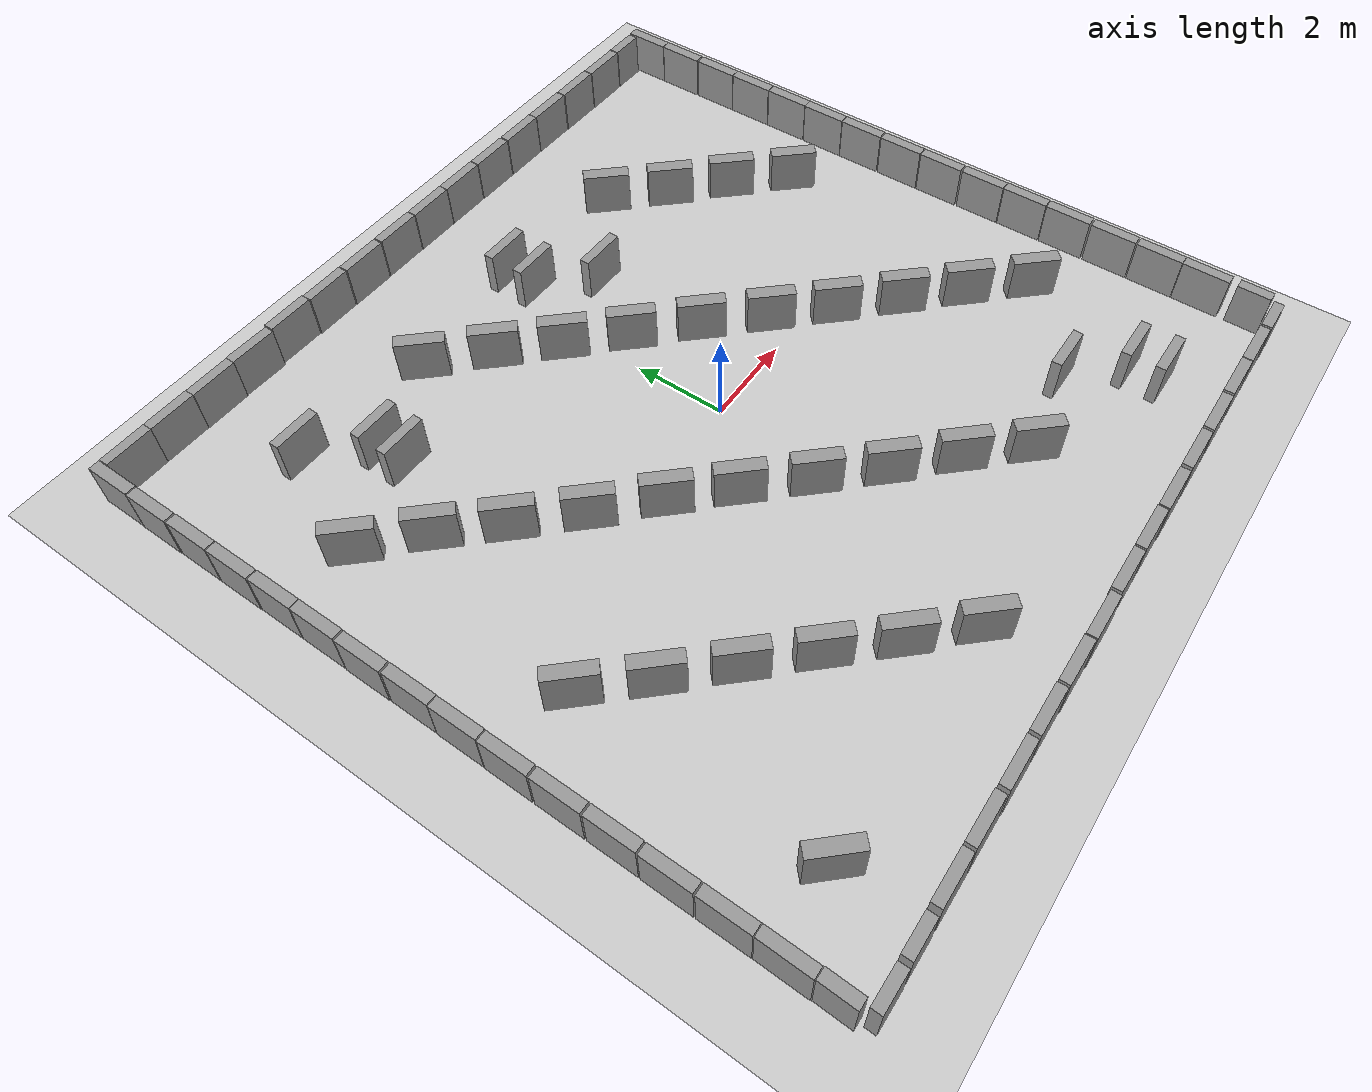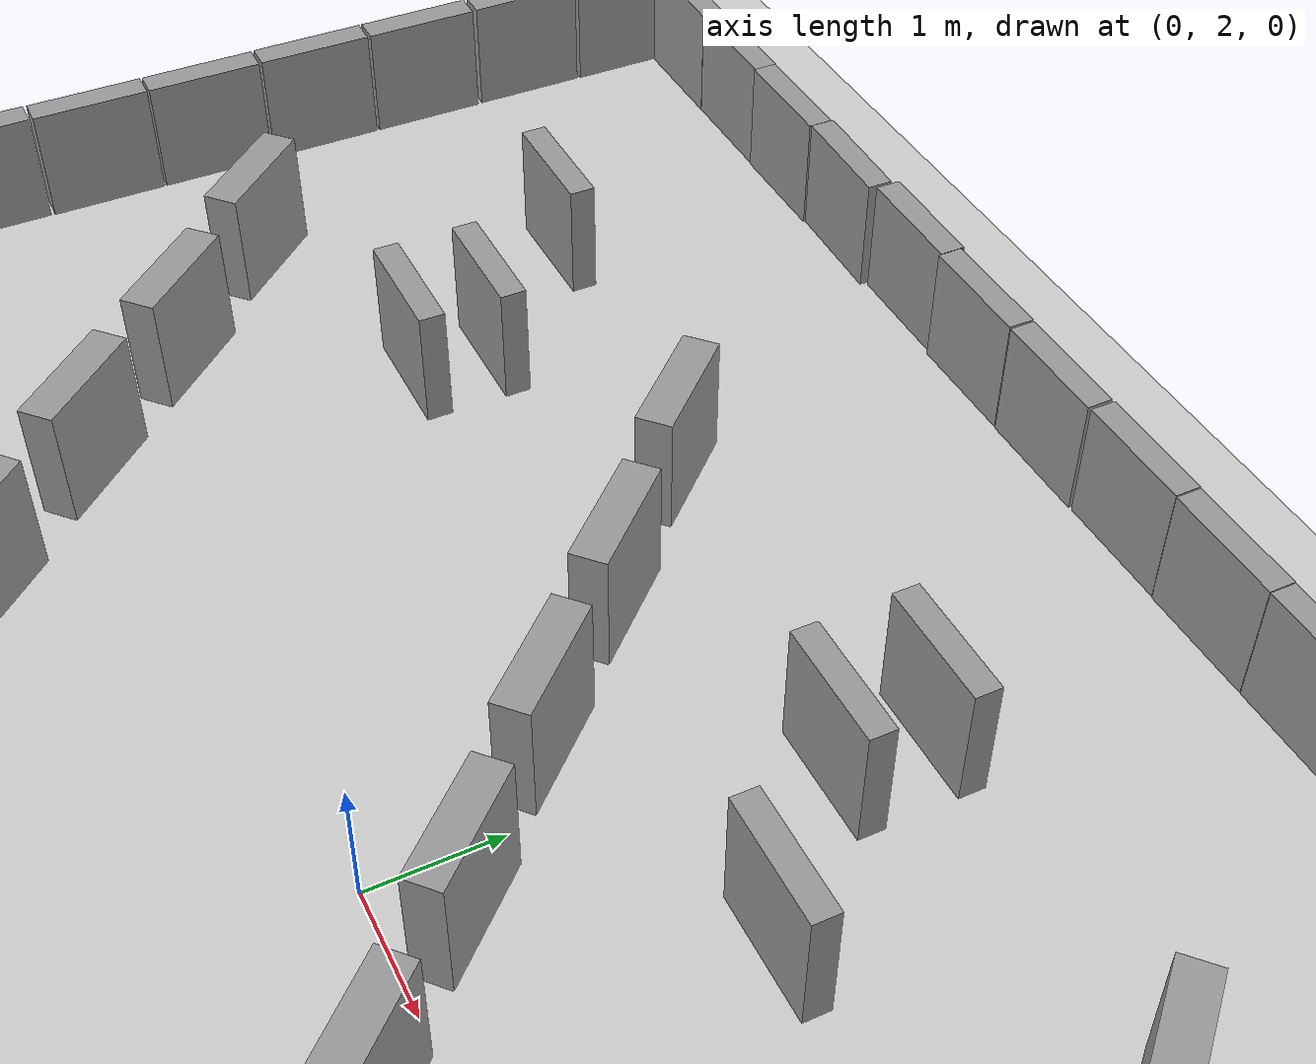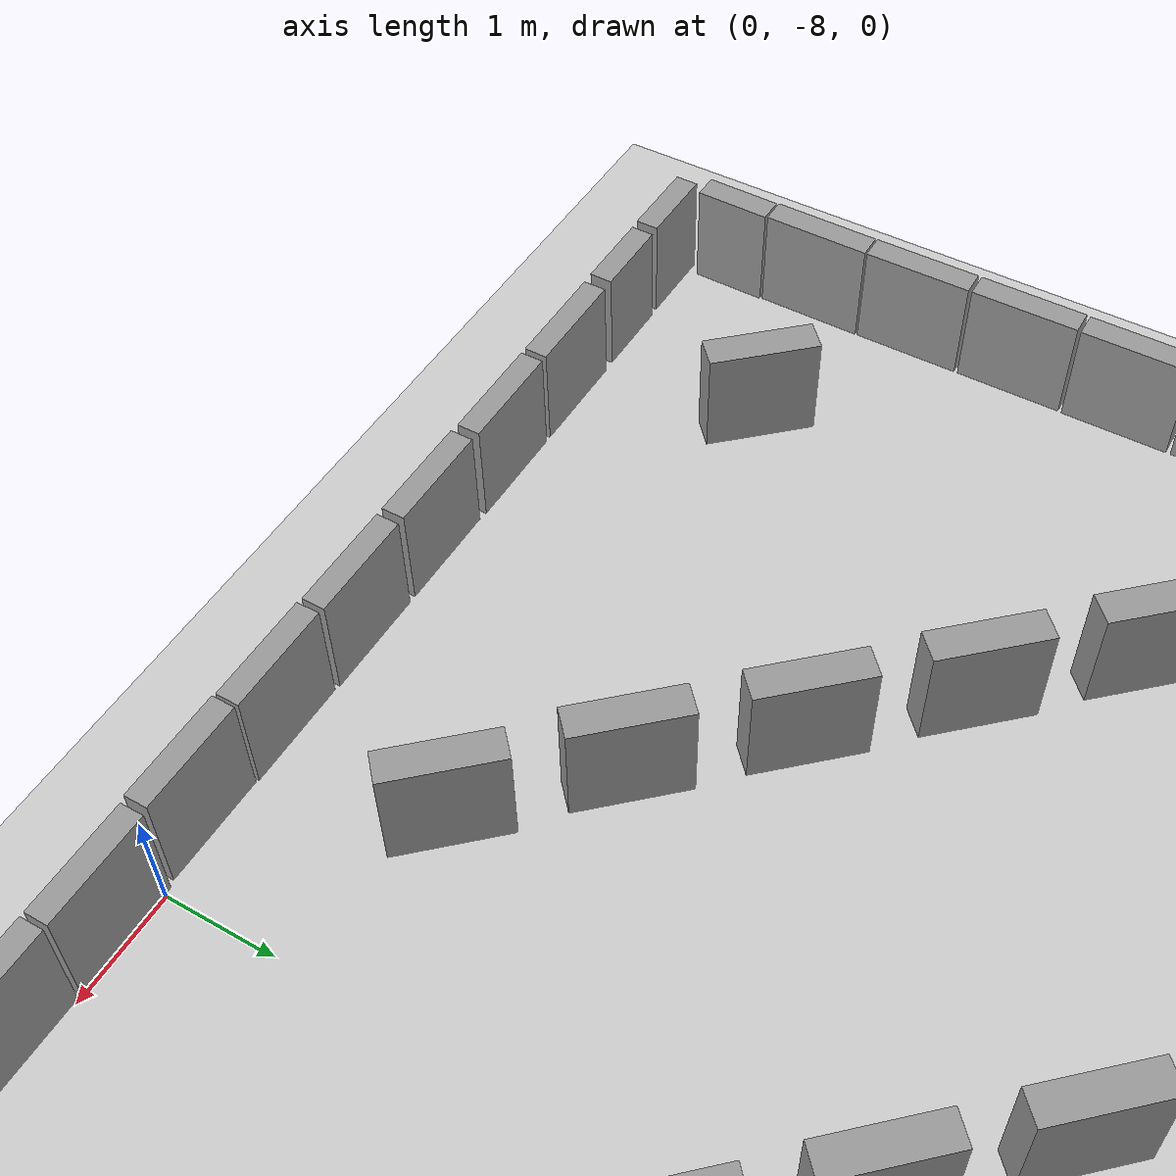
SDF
<sdf version="1.6">
 <world name="default">
  <light name="sun" type="directional">
   <pose>0 0 10 0 -0 0</pose>
   <diffuse>0.8 0.8 0.8 1</diffuse>
   <specular>0.1 0.1 0.1 1</specular>
   <attenuation>
    <range>1000</range>
    <constant>0.9</constant>
    <linear>0.01</linear>
    <quadratic>0.001</quadratic>
   </attenuation>
   <direction>-0.5 0.5 -1</direction>
  </light>
  <model name="ground_plane">
   <static>1</static>
   <static>1</static>
   <link name="link">
    <collision name="collision">
     <geometry><plane><normal>0 0 1</normal><size>100 100</size></plane></geometry>
     <surface><friction><ode><mu>100</mu><mu2>50</mu2></ode></friction></surface>
    </collision>
    <visual name="visual">
     <cast_shadows>0</cast_shadows>
     <geometry><plane><normal>0 0 1</normal><size>100 100</size></plane></geometry>
     <material>
      <script><uri>file://media/materials/scripts/gazebo.material</uri><name>Gazebo/Grey</name></script>
     </material>
    </visual>
   </link>
  </model>
  <gravity>0 0 -9.8</gravity>
  <magnetic_field>6e-06 2.3e-05 -4.2e-05</magnetic_field>
  <atmosphere type="adiabatic"/>
  <physics name="default_physics" default="0" type="ode">
   <max_step_size>0.001</max_step_size>
   <real_time_factor>1</real_time_factor>
   <real_time_update_rate>1000</real_time_update_rate>
  </physics>
  <scene><ambient>0.4 0.4 0.4 1</ambient><background>0.7 0.7 0.7 1</background><shadows>1</shadows></scene>
  <spherical_coordinates>
   <surface_model>EARTH_WGS84</surface_model>
   <latitude_deg>0</latitude_deg>
   <longitude_deg>0</longitude_deg>
   <elevation>0</elevation>
   <heading_deg>0</heading_deg>
  </spherical_coordinates>
  <audio><device>default</device></audio>
  <model name="unit_box_clone">
   <pose>-7.49845 8.11965 0.5 0 -0 0.00022</pose>
   <link name="link">
    <inertial>
     <mass>1</mass>
     <inertia>
      <ixx>0.166667</ixx>
      <ixy>0</ixy>
      <ixz>0</ixz>
      <iyy>0.166667</iyy>
      <iyz>0</iyz>
      <izz>0.166667</izz>
     </inertia>
    </inertial>
    <collision name="collision"><geometry><box><size>1 0.210541 1</size></box></geometry></collision>
    <visual name="visual">
     <geometry><box><size>1 0.210541 1</size></box></geometry>
     <material>
      <script><name>Gazebo/Grey</name><uri>file://media/materials/scripts/gazebo.material</uri></script>
     </material>
    </visual>
   </link>
  </model>
  <model name="unit_box_clone_0">
   <pose>-6.4973 8.1202 0.5 0 0 -0.002315</pose>
   <link name="link">
    <inertial>
     <mass>1</mass>
     <inertia>
      <ixx>0.166667</ixx>
      <ixy>0</ixy>
      <ixz>0</ixz>
      <iyy>0.166667</iyy>
      <iyz>0</iyz>
      <izz>0.166667</izz>
     </inertia>
    </inertial>
    <collision name="collision"><geometry><box><size>1 0.210541 1</size></box></geometry></collision>
    <visual name="visual">
     <geometry><box><size>1 0.210541 1</size></box></geometry>
     <material>
      <script><name>Gazebo/Grey</name><uri>file://media/materials/scripts/gazebo.material</uri></script>
     </material>
    </visual>
   </link>
  </model>
  <model name="unit_box_clone_1">
   <pose>-5.49732 8.10895 0.5 0 0 -0.002307</pose>
   <link name="link">
    <inertial>
     <mass>1</mass>
     <inertia>
      <ixx>0.166667</ixx>
      <ixy>0</ixy>
      <ixz>0</ixz>
      <iyy>0.166667</iyy>
      <iyz>0</iyz>
      <izz>0.166667</izz>
     </inertia>
    </inertial>
    <collision name="collision"><geometry><box><size>1 0.210541 1</size></box></geometry></collision>
    <visual name="visual">
     <geometry><box><size>1 0.210541 1</size></box></geometry>
     <material>
      <script><name>Gazebo/Grey</name><uri>file://media/materials/scripts/gazebo.material</uri></script>
     </material>
    </visual>
   </link>
  </model>
  <model name="unit_box_clone_2">
   <pose>-4.49484 8.11103 0.5 0 0 -0.026959</pose>
   <link name="link">
    <inertial>
     <mass>1</mass>
     <inertia>
      <ixx>0.166667</ixx>
      <ixy>0</ixy>
      <ixz>0</ixz>
      <iyy>0.166667</iyy>
      <iyz>0</iyz>
      <izz>0.166667</izz>
     </inertia>
    </inertial>
    <collision name="collision"><geometry><box><size>1 0.210541 1</size></box></geometry></collision>
    <visual name="visual">
     <geometry><box><size>1 0.210541 1</size></box></geometry>
     <material>
      <script><name>Gazebo/Grey</name><uri>file://media/materials/scripts/gazebo.material</uri></script>
     </material>
    </visual>
   </link>
  </model>
  <model name="unit_box_clone_3">
   <pose>-3.46835 8.14979 0.5 -0 -0 -0.007821</pose>
   <link name="link">
    <inertial>
     <mass>1</mass>
     <inertia>
      <ixx>0.166667</ixx>
      <ixy>0</ixy>
      <ixz>0</ixz>
      <iyy>0.166667</iyy>
      <iyz>0</iyz>
      <izz>0.166667</izz>
     </inertia>
    </inertial>
    <collision name="collision"><geometry><box><size>1 0.210541 1</size></box></geometry></collision>
    <visual name="visual">
     <geometry><box><size>1 0.210541 1</size></box></geometry>
     <material>
      <script><name>Gazebo/Grey</name><uri>file://media/materials/scripts/gazebo.material</uri></script>
     </material>
    </visual>
   </link>
  </model>
  <model name="unit_box_clone_4">
   <pose>-2.46316 8.11834 0.5 0 -0 0.00022</pose>
   <link name="link">
    <inertial>
     <mass>1</mass>
     <inertia>
      <ixx>0.166667</ixx>
      <ixy>0</ixy>
      <ixz>0</ixz>
      <iyy>0.166667</iyy>
      <iyz>0</iyz>
      <izz>0.166667</izz>
     </inertia>
    </inertial>
    <collision name="collision"><geometry><box><size>1 0.210541 1</size></box></geometry></collision>
    <visual name="visual">
     <geometry><box><size>1 0.210541 1</size></box></geometry>
     <material>
      <script><name>Gazebo/Grey</name><uri>file://media/materials/scripts/gazebo.material</uri></script>
     </material>
    </visual>
   </link>
  </model>
  <model name="unit_box_clone_5">
   <pose>-1.44425 8.11167 0.5 0 -0 0.00022</pose>
   <link name="link">
    <inertial>
     <mass>1</mass>
     <inertia>
      <ixx>0.166667</ixx>
      <ixy>0</ixy>
      <ixz>0</ixz>
      <iyy>0.166667</iyy>
      <iyz>0</iyz>
      <izz>0.166667</izz>
     </inertia>
    </inertial>
    <collision name="collision"><geometry><box><size>1 0.210541 1</size></box></geometry></collision>
    <visual name="visual">
     <geometry><box><size>1 0.210541 1</size></box></geometry>
     <material>
      <script><name>Gazebo/Grey</name><uri>file://media/materials/scripts/gazebo.material</uri></script>
     </material>
    </visual>
   </link>
  </model>
  <model name="unit_box_clone_6">
   <pose>-0.418684 8.11833 0.5 0 -0 0.00022</pose>
   <link name="link">
    <inertial>
     <mass>1</mass>
     <inertia>
      <ixx>0.166667</ixx>
      <ixy>0</ixy>
      <ixz>0</ixz>
      <iyy>0.166667</iyy>
      <iyz>0</iyz>
      <izz>0.166667</izz>
     </inertia>
    </inertial>
    <collision name="collision"><geometry><box><size>1 0.210541 1</size></box></geometry></collision>
    <visual name="visual">
     <geometry><box><size>1 0.210541 1</size></box></geometry>
     <material>
      <script><name>Gazebo/Grey</name><uri>file://media/materials/scripts/gazebo.material</uri></script>
     </material>
    </visual>
   </link>
  </model>
  <model name="unit_box_clone_7">
   <pose>0.592835 8.1112 0.5 0 -0 0.00022</pose>
   <link name="link">
    <inertial>
     <mass>1</mass>
     <inertia>
      <ixx>0.166667</ixx>
      <ixy>0</ixy>
      <ixz>0</ixz>
      <iyy>0.166667</iyy>
      <iyz>0</iyz>
      <izz>0.166667</izz>
     </inertia>
    </inertial>
    <collision name="collision"><geometry><box><size>1 0.210541 1</size></box></geometry></collision>
    <visual name="visual">
     <geometry><box><size>1 0.210541 1</size></box></geometry>
     <material>
      <script><name>Gazebo/Grey</name><uri>file://media/materials/scripts/gazebo.material</uri></script>
     </material>
    </visual>
   </link>
  </model>
  <model name="unit_box_clone_8">
   <pose>1.60043 8.1097 0.5 0 -0 0.00022</pose>
   <link name="link">
    <inertial>
     <mass>1</mass>
     <inertia>
      <ixx>0.166667</ixx>
      <ixy>0</ixy>
      <ixz>0</ixz>
      <iyy>0.166667</iyy>
      <iyz>0</iyz>
      <izz>0.166667</izz>
     </inertia>
    </inertial>
    <collision name="collision"><geometry><box><size>1 0.210541 1</size></box></geometry></collision>
    <visual name="visual">
     <geometry><box><size>1 0.210541 1</size></box></geometry>
     <material>
      <script><name>Gazebo/Grey</name><uri>file://media/materials/scripts/gazebo.material</uri></script>
     </material>
    </visual>
   </link>
  </model>
  <model name="unit_box_clone_9">
   <pose>2.60987 8.10252 0.5 0 -0 0.00022</pose>
   <link name="link">
    <inertial>
     <mass>1</mass>
     <inertia>
      <ixx>0.166667</ixx>
      <ixy>0</ixy>
      <ixz>0</ixz>
      <iyy>0.166667</iyy>
      <iyz>0</iyz>
      <izz>0.166667</izz>
     </inertia>
    </inertial>
    <collision name="collision"><geometry><box><size>1 0.210541 1</size></box></geometry></collision>
    <visual name="visual">
     <geometry><box><size>1 0.210541 1</size></box></geometry>
     <material>
      <script><name>Gazebo/Grey</name><uri>file://media/materials/scripts/gazebo.material</uri></script>
     </material>
    </visual>
   </link>
  </model>
  <model name="unit_box_clone_10">
   <pose>3.62649 8.09892 0.5 0 -0 0.00022</pose>
   <link name="link">
    <inertial>
     <mass>1</mass>
     <inertia>
      <ixx>0.166667</ixx>
      <ixy>0</ixy>
      <ixz>0</ixz>
      <iyy>0.166667</iyy>
      <iyz>0</iyz>
      <izz>0.166667</izz>
     </inertia>
    </inertial>
    <collision name="collision"><geometry><box><size>1 0.210541 1</size></box></geometry></collision>
    <visual name="visual">
     <geometry><box><size>1 0.210541 1</size></box></geometry>
     <material>
      <script><name>Gazebo/Grey</name><uri>file://media/materials/scripts/gazebo.material</uri></script>
     </material>
    </visual>
   </link>
  </model>
  <model name="unit_box_clone_11">
   <pose>4.6331 8.0949 0.499999 1e-06 2e-06 -0.003264</pose>
   <link name="link">
    <inertial>
     <mass>1</mass>
     <inertia>
      <ixx>0.166667</ixx>
      <ixy>0</ixy>
      <ixz>0</ixz>
      <iyy>0.166667</iyy>
      <iyz>0</iyz>
      <izz>0.166667</izz>
     </inertia>
    </inertial>
    <collision name="collision"><geometry><box><size>1 0.210541 1</size></box></geometry></collision>
    <visual name="visual">
     <geometry><box><size>1 0.210541 1</size></box></geometry>
     <material>
      <script><name>Gazebo/Grey</name><uri>file://media/materials/scripts/gazebo.material</uri></script>
     </material>
    </visual>
   </link>
  </model>
  <model name="unit_box_0_clone_0">
   <pose>8.11522 6.68458 0.5 1e-06 1e-06 -0.000394</pose>
   <link name="link">
    <inertial>
     <mass>1</mass>
     <inertia>
      <ixx>0.166667</ixx>
      <ixy>0</ixy>
      <ixz>0</ixz>
      <iyy>0.166667</iyy>
      <iyz>0</iyz>
      <izz>0.166667</izz>
     </inertia>
    </inertial>
    <collision name="collision"><geometry><box><size>0.230819 1 1</size></box></geometry></collision>
    <visual name="visual">
     <geometry><box><size>0.230819 1 1</size></box></geometry>
     <material>
      <script><name>Gazebo/Grey</name><uri>file://media/materials/scripts/gazebo.material</uri></script>
     </material>
    </visual>
   </link>
  </model>
  <model name="unit_box_0_clone_1">
   <pose>8.11915 5.6517 0.5 -1e-06 -1e-06 0.000117</pose>
   <link name="link">
    <inertial>
     <mass>1</mass>
     <inertia>
      <ixx>0.166667</ixx>
      <ixy>0</ixy>
      <ixz>0</ixz>
      <iyy>0.166667</iyy>
      <iyz>0</iyz>
      <izz>0.166667</izz>
     </inertia>
    </inertial>
    <collision name="collision"><geometry><box><size>0.230819 1 1</size></box></geometry></collision>
    <visual name="visual">
     <geometry><box><size>0.230819 1 1</size></box></geometry>
     <material>
      <script><name>Gazebo/Grey</name><uri>file://media/materials/scripts/gazebo.material</uri></script>
     </material>
    </visual>
   </link>
  </model>
  <model name="unit_box_0_clone_2">
   <pose>8.11914 4.64016 0.5 -1e-06 -1e-06 0.000211</pose>
   <link name="link">
    <inertial>
     <mass>1</mass>
     <inertia>
      <ixx>0.166667</ixx>
      <ixy>0</ixy>
      <ixz>0</ixz>
      <iyy>0.166667</iyy>
      <iyz>0</iyz>
      <izz>0.166667</izz>
     </inertia>
    </inertial>
    <collision name="collision"><geometry><box><size>0.230819 1 1</size></box></geometry></collision>
    <visual name="visual">
     <geometry><box><size>0.230819 1 1</size></box></geometry>
     <material>
      <script><name>Gazebo/Grey</name><uri>file://media/materials/scripts/gazebo.material</uri></script>
     </material>
    </visual>
   </link>
  </model>
  <model name="unit_box_0_clone_3">
   <pose>8.11914 3.62228 0.5 -1e-06 -1e-06 0.000192</pose>
   <link name="link">
    <inertial>
     <mass>1</mass>
     <inertia>
      <ixx>0.166667</ixx>
      <ixy>0</ixy>
      <ixz>0</ixz>
      <iyy>0.166667</iyy>
      <iyz>0</iyz>
      <izz>0.166667</izz>
     </inertia>
    </inertial>
    <collision name="collision"><geometry><box><size>0.230819 1 1</size></box></geometry></collision>
    <visual name="visual">
     <geometry><box><size>0.230819 1 1</size></box></geometry>
     <material>
      <script><name>Gazebo/Grey</name><uri>file://media/materials/scripts/gazebo.material</uri></script>
     </material>
    </visual>
   </link>
  </model>
  <model name="unit_box_0_clone_4">
   <pose>8.11332 2.61063 0.5 -1e-06 1e-06 -0.001062</pose>
   <link name="link">
    <inertial>
     <mass>1</mass>
     <inertia>
      <ixx>0.166667</ixx>
      <ixy>0</ixy>
      <ixz>0</ixz>
      <iyy>0.166667</iyy>
      <iyz>0</iyz>
      <izz>0.166667</izz>
     </inertia>
    </inertial>
    <collision name="collision"><geometry><box><size>0.230819 1 1</size></box></geometry></collision>
    <visual name="visual">
     <geometry><box><size>0.230819 1 1</size></box></geometry>
     <material>
      <script><name>Gazebo/Grey</name><uri>file://media/materials/scripts/gazebo.material</uri></script>
     </material>
    </visual>
   </link>
  </model>
  <model name="unit_box_0_clone_5">
   <pose>8.11277 1.59919 0.5 -1e-06 -1e-06 0.000192</pose>
   <link name="link">
    <inertial>
     <mass>1</mass>
     <inertia>
      <ixx>0.166667</ixx>
      <ixy>0</ixy>
      <ixz>0</ixz>
      <iyy>0.166667</iyy>
      <iyz>0</iyz>
      <izz>0.166667</izz>
     </inertia>
    </inertial>
    <collision name="collision"><geometry><box><size>0.230819 1 1</size></box></geometry></collision>
    <visual name="visual">
     <geometry><box><size>0.230819 1 1</size></box></geometry>
     <material>
      <script><name>Gazebo/Grey</name><uri>file://media/materials/scripts/gazebo.material</uri></script>
     </material>
    </visual>
   </link>
  </model>
  <model name="unit_box_0_clone_6">
   <pose>8.11277 0.574938 0.5 -1e-06 -1e-06 0.000192</pose>
   <link name="link">
    <inertial>
     <mass>1</mass>
     <inertia>
      <ixx>0.166667</ixx>
      <ixy>0</ixy>
      <ixz>0</ixz>
      <iyy>0.166667</iyy>
      <iyz>0</iyz>
      <izz>0.166667</izz>
     </inertia>
    </inertial>
    <collision name="collision"><geometry><box><size>0.230819 1 1</size></box></geometry></collision>
    <visual name="visual">
     <geometry><box><size>0.230819 1 1</size></box></geometry>
     <material>
      <script><name>Gazebo/Grey</name><uri>file://media/materials/scripts/gazebo.material</uri></script>
     </material>
    </visual>
   </link>
  </model>
  <model name="unit_box_0_clone_7">
   <pose>8.11276 -0.44932 0.5 -1e-06 -1e-06 0.000192</pose>
   <link name="link">
    <inertial>
     <mass>1</mass>
     <inertia>
      <ixx>0.166667</ixx>
      <ixy>0</ixy>
      <ixz>0</ixz>
      <iyy>0.166667</iyy>
      <iyz>0</iyz>
      <izz>0.166667</izz>
     </inertia>
    </inertial>
    <collision name="collision"><geometry><box><size>0.230819 1 1</size></box></geometry></collision>
    <visual name="visual">
     <geometry><box><size>0.230819 1 1</size></box></geometry>
     <material>
      <script><name>Gazebo/Grey</name><uri>file://media/materials/scripts/gazebo.material</uri></script>
     </material>
    </visual>
   </link>
  </model>
  <model name="unit_box_0_clone_8">
   <pose>8.11912 -1.48629 0.5 -1e-06 -1e-06 0.000192</pose>
   <link name="link">
    <inertial>
     <mass>1</mass>
     <inertia>
      <ixx>0.166667</ixx>
      <ixy>0</ixy>
      <ixz>0</ixz>
      <iyy>0.166667</iyy>
      <iyz>0</iyz>
      <izz>0.166667</izz>
     </inertia>
    </inertial>
    <collision name="collision"><geometry><box><size>0.230819 1 1</size></box></geometry></collision>
    <visual name="visual">
     <geometry><box><size>0.230819 1 1</size></box></geometry>
     <material>
      <script><name>Gazebo/Grey</name><uri>file://media/materials/scripts/gazebo.material</uri></script>
     </material>
    </visual>
   </link>
  </model>
  <model name="unit_box_0_clone_9">
   <pose>8.12548 -2.5042 0.5 -1e-06 -1e-06 0.000192</pose>
   <link name="link">
    <inertial>
     <mass>1</mass>
     <inertia>
      <ixx>0.166667</ixx>
      <ixy>0</ixy>
      <ixz>0</ixz>
      <iyy>0.166667</iyy>
      <iyz>0</iyz>
      <izz>0.166667</izz>
     </inertia>
    </inertial>
    <collision name="collision"><geometry><box><size>0.230819 1 1</size></box></geometry></collision>
    <visual name="visual">
     <geometry><box><size>0.230819 1 1</size></box></geometry>
     <material>
      <script><name>Gazebo/Grey</name><uri>file://media/materials/scripts/gazebo.material</uri></script>
     </material>
    </visual>
   </link>
  </model>
  <model name="unit_box_0_clone_10">
   <pose>8.12331 -3.52223 0.5 -1e-06 -1e-06 0.000192</pose>
   <link name="link">
    <inertial>
     <mass>1</mass>
     <inertia>
      <ixx>0.166667</ixx>
      <ixy>0</ixy>
      <ixz>0</ixz>
      <iyy>0.166667</iyy>
      <iyz>0</iyz>
      <izz>0.166667</izz>
     </inertia>
    </inertial>
    <collision name="collision"><geometry><box><size>0.230819 1 1</size></box></geometry></collision>
    <visual name="visual">
     <geometry><box><size>0.230819 1 1</size></box></geometry>
     <material>
      <script><name>Gazebo/Grey</name><uri>file://media/materials/scripts/gazebo.material</uri></script>
     </material>
    </visual>
   </link>
  </model>
  <model name="unit_box_0_clone_11">
   <pose>8.1233 -4.56316 0.5 -1e-06 -1e-06 0.000192</pose>
   <link name="link">
    <inertial>
     <mass>1</mass>
     <inertia>
      <ixx>0.166667</ixx>
      <ixy>0</ixy>
      <ixz>0</ixz>
      <iyy>0.166667</iyy>
      <iyz>0</iyz>
      <izz>0.166667</izz>
     </inertia>
    </inertial>
    <collision name="collision"><geometry><box><size>0.230819 1 1</size></box></geometry></collision>
    <visual name="visual">
     <geometry><box><size>0.230819 1 1</size></box></geometry>
     <material>
      <script><name>Gazebo/Grey</name><uri>file://media/materials/scripts/gazebo.material</uri></script>
     </material>
    </visual>
   </link>
  </model>
  <model name="unit_box_0_clone_12">
   <pose>8.11815 -5.59377 0.5 -1e-06 -1e-06 0.000192</pose>
   <link name="link">
    <inertial>
     <mass>1</mass>
     <inertia>
      <ixx>0.166667</ixx>
      <ixy>0</ixy>
      <ixz>0</ixz>
      <iyy>0.166667</iyy>
      <iyz>0</iyz>
      <izz>0.166667</izz>
     </inertia>
    </inertial>
    <collision name="collision"><geometry><box><size>0.230819 1 1</size></box></geometry></collision>
    <visual name="visual">
     <geometry><box><size>0.230819 1 1</size></box></geometry>
     <material>
      <script><name>Gazebo/Grey</name><uri>file://media/materials/scripts/gazebo.material</uri></script>
     </material>
    </visual>
   </link>
  </model>
  <model name="unit_box_0_clone_13">
   <pose>8.11333 -6.60776 0.5 0 -0 -0.005474</pose>
   <link name="link">
    <inertial>
     <mass>1</mass>
     <inertia>
      <ixx>0.166667</ixx>
      <ixy>0</ixy>
      <ixz>0</ixz>
      <iyy>0.166667</iyy>
      <iyz>0</iyz>
      <izz>0.166667</izz>
     </inertia>
    </inertial>
    <collision name="collision"><geometry><box><size>0.230819 1 1</size></box></geometry></collision>
    <visual name="visual">
     <geometry><box><size>0.230819 1 1</size></box></geometry>
     <material>
      <script><name>Gazebo/Grey</name><uri>file://media/materials/scripts/gazebo.material</uri></script>
     </material>
    </visual>
   </link>
  </model>
  <model name="unit_box_clone_15_clone_0">
   <pose>6.71207 -8.13139 0.5 0 -0 0.00022</pose>
   <link name="link">
    <inertial>
     <mass>1</mass>
     <inertia>
      <ixx>0.166667</ixx>
      <ixy>0</ixy>
      <ixz>0</ixz>
      <iyy>0.166667</iyy>
      <iyz>0</iyz>
      <izz>0.166667</izz>
     </inertia>
    </inertial>
    <collision name="collision"><geometry><box><size>1 0.210541 1</size></box></geometry></collision>
    <visual name="visual">
     <geometry><box><size>1 0.210541 1</size></box></geometry>
     <material>
      <script><name>Gazebo/Grey</name><uri>file://media/materials/scripts/gazebo.material</uri></script>
     </material>
    </visual>
   </link>
  </model>
  <model name="unit_box_clone_15_clone_1">
   <pose>5.69715 -8.13138 0.5 0 -0 0.00022</pose>
   <link name="link">
    <inertial>
     <mass>1</mass>
     <inertia>
      <ixx>0.166667</ixx>
      <ixy>0</ixy>
      <ixz>0</ixz>
      <iyy>0.166667</iyy>
      <iyz>0</iyz>
      <izz>0.166667</izz>
     </inertia>
    </inertial>
    <collision name="collision"><geometry><box><size>1 0.210541 1</size></box></geometry></collision>
    <visual name="visual">
     <geometry><box><size>1 0.210541 1</size></box></geometry>
     <material>
      <script><name>Gazebo/Grey</name><uri>file://media/materials/scripts/gazebo.material</uri></script>
     </material>
    </visual>
   </link>
  </model>
  <model name="unit_box_clone_15_clone_2">
   <pose>4.63881 -8.13757 0.5 0 -0 0.00022</pose>
   <link name="link">
    <inertial>
     <mass>1</mass>
     <inertia>
      <ixx>0.166667</ixx>
      <ixy>0</ixy>
      <ixz>0</ixz>
      <iyy>0.166667</iyy>
      <iyz>0</iyz>
      <izz>0.166667</izz>
     </inertia>
    </inertial>
    <collision name="collision"><geometry><box><size>1 0.210541 1</size></box></geometry></collision>
    <visual name="visual">
     <geometry><box><size>1 0.210541 1</size></box></geometry>
     <material>
      <script><name>Gazebo/Grey</name><uri>file://media/materials/scripts/gazebo.material</uri></script>
     </material>
    </visual>
   </link>
  </model>
  <model name="unit_box_clone_15_clone_3">
   <pose>3.57975 -8.13757 0.5 0 -0 0.00022</pose>
   <link name="link">
    <inertial>
     <mass>1</mass>
     <inertia>
      <ixx>0.166667</ixx>
      <ixy>0</ixy>
      <ixz>0</ixz>
      <iyy>0.166667</iyy>
      <iyz>0</iyz>
      <izz>0.166667</izz>
     </inertia>
    </inertial>
    <collision name="collision"><geometry><box><size>1 0.210541 1</size></box></geometry></collision>
    <visual name="visual">
     <geometry><box><size>1 0.210541 1</size></box></geometry>
     <material>
      <script><name>Gazebo/Grey</name><uri>file://media/materials/scripts/gazebo.material</uri></script>
     </material>
    </visual>
   </link>
  </model>
  <model name="unit_box_clone_15_clone_4">
   <pose>2.49815 -8.13756 0.5 0 -0 0.00022</pose>
   <link name="link">
    <inertial>
     <mass>1</mass>
     <inertia>
      <ixx>0.166667</ixx>
      <ixy>0</ixy>
      <ixz>0</ixz>
      <iyy>0.166667</iyy>
      <iyz>0</iyz>
      <izz>0.166667</izz>
     </inertia>
    </inertial>
    <collision name="collision"><geometry><box><size>1 0.210541 1</size></box></geometry></collision>
    <visual name="visual">
     <geometry><box><size>1 0.210541 1</size></box></geometry>
     <material>
      <script><name>Gazebo/Grey</name><uri>file://media/materials/scripts/gazebo.material</uri></script>
     </material>
    </visual>
   </link>
  </model>
  <model name="unit_box_clone_15_clone_5">
   <pose>1.46162 -8.12628 0.5 0 -0 0.00022</pose>
   <link name="link">
    <inertial>
     <mass>1</mass>
     <inertia>
      <ixx>0.166667</ixx>
      <ixy>0</ixy>
      <ixz>0</ixz>
      <iyy>0.166667</iyy>
      <iyz>0</iyz>
      <izz>0.166667</izz>
     </inertia>
    </inertial>
    <collision name="collision"><geometry><box><size>1 0.210541 1</size></box></geometry></collision>
    <visual name="visual">
     <geometry><box><size>1 0.210541 1</size></box></geometry>
     <material>
      <script><name>Gazebo/Grey</name><uri>file://media/materials/scripts/gazebo.material</uri></script>
     </material>
    </visual>
   </link>
  </model>
  <model name="unit_box_clone_15_clone_6">
   <pose>0.425088 -8.12627 0.5 0 -0 0.00022</pose>
   <link name="link">
    <inertial>
     <mass>1</mass>
     <inertia>
      <ixx>0.166667</ixx>
      <ixy>0</ixy>
      <ixz>0</ixz>
      <iyy>0.166667</iyy>
      <iyz>0</iyz>
      <izz>0.166667</izz>
     </inertia>
    </inertial>
    <collision name="collision"><geometry><box><size>1 0.210541 1</size></box></geometry></collision>
    <visual name="visual">
     <geometry><box><size>1 0.210541 1</size></box></geometry>
     <material>
      <script><name>Gazebo/Grey</name><uri>file://media/materials/scripts/gazebo.material</uri></script>
     </material>
    </visual>
   </link>
  </model>
  <model name="unit_box_clone_15_clone_7">
   <pose>-0.633974 -8.14883 0.5 0 -0 0.00022</pose>
   <link name="link">
    <inertial>
     <mass>1</mass>
     <inertia>
      <ixx>0.166667</ixx>
      <ixy>0</ixy>
      <ixz>0</ixz>
      <iyy>0.166667</iyy>
      <iyz>0</iyz>
      <izz>0.166667</izz>
     </inertia>
    </inertial>
    <collision name="collision"><geometry><box><size>1 0.210541 1</size></box></geometry></collision>
    <visual name="visual">
     <geometry><box><size>1 0.210541 1</size></box></geometry>
     <material>
      <script><name>Gazebo/Grey</name><uri>file://media/materials/scripts/gazebo.material</uri></script>
     </material>
    </visual>
   </link>
  </model>
  <model name="unit_box_clone_15_clone_8">
   <pose>-1.65923 -8.13754 0.5 0 -0 0.00022</pose>
   <link name="link">
    <inertial>
     <mass>1</mass>
     <inertia>
      <ixx>0.166667</ixx>
      <ixy>0</ixy>
      <ixz>0</ixz>
      <iyy>0.166667</iyy>
      <iyz>0</iyz>
      <izz>0.166667</izz>
     </inertia>
    </inertial>
    <collision name="collision"><geometry><box><size>1 0.210541 1</size></box></geometry></collision>
    <visual name="visual">
     <geometry><box><size>1 0.210541 1</size></box></geometry>
     <material>
      <script><name>Gazebo/Grey</name><uri>file://media/materials/scripts/gazebo.material</uri></script>
     </material>
    </visual>
   </link>
  </model>
  <model name="unit_box_clone_15_clone_9">
   <pose>-2.70703 -8.1263 0.5 0 -0 0.00022</pose>
   <link name="link">
    <inertial>
     <mass>1</mass>
     <inertia>
      <ixx>0.166667</ixx>
      <ixy>0</ixy>
      <ixz>0</ixz>
      <iyy>0.166667</iyy>
      <iyz>0</iyz>
      <izz>0.166667</izz>
     </inertia>
    </inertial>
    <collision name="collision"><geometry><box><size>1 0.210541 1</size></box></geometry></collision>
    <visual name="visual">
     <geometry><box><size>1 0.210541 1</size></box></geometry>
     <material>
      <script><name>Gazebo/Grey</name><uri>file://media/materials/scripts/gazebo.material</uri></script>
     </material>
    </visual>
   </link>
  </model>
  <model name="unit_box_clone_15_clone_10">
   <pose>-3.77736 -8.12628 0.5 0 -0 0.00022</pose>
   <link name="link">
    <inertial>
     <mass>1</mass>
     <inertia>
      <ixx>0.166667</ixx>
      <ixy>0</ixy>
      <ixz>0</ixz>
      <iyy>0.166667</iyy>
      <iyz>0</iyz>
      <izz>0.166667</izz>
     </inertia>
    </inertial>
    <collision name="collision"><geometry><box><size>1 0.210541 1</size></box></geometry></collision>
    <visual name="visual">
     <geometry><box><size>1 0.210541 1</size></box></geometry>
     <material>
      <script><name>Gazebo/Grey</name><uri>file://media/materials/scripts/gazebo.material</uri></script>
     </material>
    </visual>
   </link>
  </model>
  <model name="unit_box_clone_15_clone_11">
   <pose>-4.85896 -8.11502 0.5 0 -0 0.00022</pose>
   <link name="link">
    <inertial>
     <mass>1</mass>
     <inertia>
      <ixx>0.166667</ixx>
      <ixy>0</ixy>
      <ixz>0</ixz>
      <iyy>0.166667</iyy>
      <iyz>0</iyz>
      <izz>0.166667</izz>
     </inertia>
    </inertial>
    <collision name="collision"><geometry><box><size>1 0.210541 1</size></box></geometry></collision>
    <visual name="visual">
     <geometry><box><size>1 0.210541 1</size></box></geometry>
     <material>
      <script><name>Gazebo/Grey</name><uri>file://media/materials/scripts/gazebo.material</uri></script>
     </material>
    </visual>
   </link>
  </model>
  <model name="unit_box_clone_15_clone_12">
   <pose>-5.91802 -8.11501 0.5 0 -0 0.00022</pose>
   <link name="link">
    <inertial>
     <mass>1</mass>
     <inertia>
      <ixx>0.166667</ixx>
      <ixy>0</ixy>
      <ixz>0</ixz>
      <iyy>0.166667</iyy>
      <iyz>0</iyz>
      <izz>0.166667</izz>
     </inertia>
    </inertial>
    <collision name="collision"><geometry><box><size>1 0.210541 1</size></box></geometry></collision>
    <visual name="visual">
     <geometry><box><size>1 0.210541 1</size></box></geometry>
     <material>
      <script><name>Gazebo/Grey</name><uri>file://media/materials/scripts/gazebo.material</uri></script>
     </material>
    </visual>
   </link>
  </model>
  <model name="unit_box_0_clone_4_clone">
   <pose>-8.12647 7.71769 0.5 -1e-06 -1e-06 0.000192</pose>
   <link name="link">
    <inertial>
     <mass>1</mass>
     <inertia>
      <ixx>0.166667</ixx>
      <ixy>0</ixy>
      <ixz>0</ixz>
      <iyy>0.166667</iyy>
      <iyz>0</iyz>
      <izz>0.166667</izz>
     </inertia>
    </inertial>
    <collision name="collision"><geometry><box><size>0.230819 1 1</size></box></geometry></collision>
    <visual name="visual">
     <geometry><box><size>0.230819 1 1</size></box></geometry>
     <material>
      <script><name>Gazebo/Grey</name><uri>file://media/materials/scripts/gazebo.material</uri></script>
     </material>
    </visual>
   </link>
  </model>
  <model name="unit_box_0_clone_4_clone_0">
   <pose>-8.13281 6.68715 0.5 -1e-06 -1e-06 0.000192</pose>
   <link name="link">
    <inertial>
     <mass>1</mass>
     <inertia>
      <ixx>0.166667</ixx>
      <ixy>0</ixy>
      <ixz>0</ixz>
      <iyy>0.166667</iyy>
      <iyz>0</iyz>
      <izz>0.166667</izz>
     </inertia>
    </inertial>
    <collision name="collision"><geometry><box><size>0.230819 1 1</size></box></geometry></collision>
    <visual name="visual">
     <geometry><box><size>0.230819 1 1</size></box></geometry>
     <material>
      <script><name>Gazebo/Grey</name><uri>file://media/materials/scripts/gazebo.material</uri></script>
     </material>
    </visual>
   </link>
  </model>
  <model name="unit_box_0_clone_4_clone_1">
   <pose>-8.12606 5.64722 0.5 -1e-06 -1e-06 0.000192</pose>
   <link name="link">
    <inertial>
     <mass>1</mass>
     <inertia>
      <ixx>0.166667</ixx>
      <ixy>0</ixy>
      <ixz>0</ixz>
      <iyy>0.166667</iyy>
      <iyz>0</iyz>
      <izz>0.166667</izz>
     </inertia>
    </inertial>
    <collision name="collision"><geometry><box><size>0.230819 1 1</size></box></geometry></collision>
    <visual name="visual">
     <geometry><box><size>0.230819 1 1</size></box></geometry>
     <material>
      <script><name>Gazebo/Grey</name><uri>file://media/materials/scripts/gazebo.material</uri></script>
     </material>
    </visual>
   </link>
  </model>
  <model name="unit_box_0_clone_4_clone_2">
   <pose>-8.12607 4.6208 0.5 -1e-06 -1e-06 0.000192</pose>
   <link name="link">
    <inertial>
     <mass>1</mass>
     <inertia>
      <ixx>0.166667</ixx>
      <ixy>0</ixy>
      <ixz>0</ixz>
      <iyy>0.166667</iyy>
      <iyz>0</iyz>
      <izz>0.166667</izz>
     </inertia>
    </inertial>
    <collision name="collision"><geometry><box><size>0.230819 1 1</size></box></geometry></collision>
    <visual name="visual">
     <geometry><box><size>0.230819 1 1</size></box></geometry>
     <material>
      <script><name>Gazebo/Grey</name><uri>file://media/materials/scripts/gazebo.material</uri></script>
     </material>
    </visual>
   </link>
  </model>
  <model name="unit_box_0_clone_4_clone_3">
   <pose>-8.11932 3.59437 0.5 -1e-06 -1e-06 0.000192</pose>
   <link name="link">
    <inertial>
     <mass>1</mass>
     <inertia>
      <ixx>0.166667</ixx>
      <ixy>0</ixy>
      <ixz>0</ixz>
      <iyy>0.166667</iyy>
      <iyz>0</iyz>
      <izz>0.166667</izz>
     </inertia>
    </inertial>
    <collision name="collision"><geometry><box><size>0.230819 1 1</size></box></geometry></collision>
    <visual name="visual">
     <geometry><box><size>0.230819 1 1</size></box></geometry>
     <material>
      <script><name>Gazebo/Grey</name><uri>file://media/materials/scripts/gazebo.material</uri></script>
     </material>
    </visual>
   </link>
  </model>
  <model name="unit_box_0_clone_4_clone_4">
   <pose>-8.11932 2.57471 0.5 -1e-06 -1e-06 0.000192</pose>
   <link name="link">
    <inertial>
     <mass>1</mass>
     <inertia>
      <ixx>0.166667</ixx>
      <ixy>0</ixy>
      <ixz>0</ixz>
      <iyy>0.166667</iyy>
      <iyz>0</iyz>
      <izz>0.166667</izz>
     </inertia>
    </inertial>
    <collision name="collision"><geometry><box><size>0.230819 1 1</size></box></geometry></collision>
    <visual name="visual">
     <geometry><box><size>0.230819 1 1</size></box></geometry>
     <material>
      <script><name>Gazebo/Grey</name><uri>file://media/materials/scripts/gazebo.material</uri></script>
     </material>
    </visual>
   </link>
  </model>
  <model name="unit_box_0_clone_4_clone_5">
   <pose>-8.12608 1.54157 0.5 -1e-06 -1e-06 0.000192</pose>
   <link name="link">
    <inertial>
     <mass>1</mass>
     <inertia>
      <ixx>0.166667</ixx>
      <ixy>0</ixy>
      <ixz>0</ixz>
      <iyy>0.166667</iyy>
      <iyz>0</iyz>
      <izz>0.166667</izz>
     </inertia>
    </inertial>
    <collision name="collision"><geometry><box><size>0.230819 1 1</size></box></geometry></collision>
    <visual name="visual">
     <geometry><box><size>0.230819 1 1</size></box></geometry>
     <material>
      <script><name>Gazebo/Grey</name><uri>file://media/materials/scripts/gazebo.material</uri></script>
     </material>
    </visual>
   </link>
  </model>
  <model name="unit_box_0_clone_4_clone_6">
   <pose>-8.11933 0.50163 0.5 -1e-06 -1e-06 0.000192</pose>
   <link name="link">
    <inertial>
     <mass>1</mass>
     <inertia>
      <ixx>0.166667</ixx>
      <ixy>0</ixy>
      <ixz>0</ixz>
      <iyy>0.166667</iyy>
      <iyz>0</iyz>
      <izz>0.166667</izz>
     </inertia>
    </inertial>
    <collision name="collision"><geometry><box><size>0.230819 1 1</size></box></geometry></collision>
    <visual name="visual">
     <geometry><box><size>0.230819 1 1</size></box></geometry>
     <material>
      <script><name>Gazebo/Grey</name><uri>file://media/materials/scripts/gazebo.material</uri></script>
     </material>
    </visual>
   </link>
  </model>
  <model name="unit_box_0_clone_4_clone_7">
   <pose>-8.12609 -0.518034 0.5 -1e-06 -1e-06 0.000192</pose>
   <link name="link">
    <inertial>
     <mass>1</mass>
     <inertia>
      <ixx>0.166667</ixx>
      <ixy>0</ixy>
      <ixz>0</ixz>
      <iyy>0.166667</iyy>
      <iyz>0</iyz>
      <izz>0.166667</izz>
     </inertia>
    </inertial>
    <collision name="collision"><geometry><box><size>0.230819 1 1</size></box></geometry></collision>
    <visual name="visual">
     <geometry><box><size>0.230819 1 1</size></box></geometry>
     <material>
      <script><name>Gazebo/Grey</name><uri>file://media/materials/scripts/gazebo.material</uri></script>
     </material>
    </visual>
   </link>
  </model>
  <model name="unit_box_0_clone_4_clone_8">
   <pose>-8.13284 -1.54445 0.5 -1e-06 -1e-06 0.000192</pose>
   <link name="link">
    <inertial>
     <mass>1</mass>
     <inertia>
      <ixx>0.166667</ixx>
      <ixy>0</ixy>
      <ixz>0</ixz>
      <iyy>0.166667</iyy>
      <iyz>0</iyz>
      <izz>0.166667</izz>
     </inertia>
    </inertial>
    <collision name="collision"><geometry><box><size>0.230819 1 1</size></box></geometry></collision>
    <visual name="visual">
     <geometry><box><size>0.230819 1 1</size></box></geometry>
     <material>
      <script><name>Gazebo/Grey</name><uri>file://media/materials/scripts/gazebo.material</uri></script>
     </material>
    </visual>
   </link>
  </model>
  <model name="unit_box_0_clone_4_clone_9">
   <pose>-8.13285 -2.58439 0.5 -1e-06 -1e-06 0.000192</pose>
   <link name="link">
    <inertial>
     <mass>1</mass>
     <inertia>
      <ixx>0.166667</ixx>
      <ixy>0</ixy>
      <ixz>0</ixz>
      <iyy>0.166667</iyy>
      <iyz>0</iyz>
      <izz>0.166667</izz>
     </inertia>
    </inertial>
    <collision name="collision"><geometry><box><size>0.230819 1 1</size></box></geometry></collision>
    <visual name="visual">
     <geometry><box><size>0.230819 1 1</size></box></geometry>
     <material>
      <script><name>Gazebo/Grey</name><uri>file://media/materials/scripts/gazebo.material</uri></script>
     </material>
    </visual>
   </link>
  </model>
  <model name="unit_box_0_clone_4_clone_10">
   <pose>-8.13285 -3.62431 0.5 -1e-06 -1e-06 0.000192</pose>
   <link name="link">
    <inertial>
     <mass>1</mass>
     <inertia>
      <ixx>0.166667</ixx>
      <ixy>0</ixy>
      <ixz>0</ixz>
      <iyy>0.166667</iyy>
      <iyz>0</iyz>
      <izz>0.166667</izz>
     </inertia>
    </inertial>
    <collision name="collision"><geometry><box><size>0.230819 1 1</size></box></geometry></collision>
    <visual name="visual">
     <geometry><box><size>0.230819 1 1</size></box></geometry>
     <material>
      <script><name>Gazebo/Grey</name><uri>file://media/materials/scripts/gazebo.material</uri></script>
     </material>
    </visual>
   </link>
  </model>
  <model name="unit_box_0_clone_4_clone_11">
   <pose>-8.1396 -4.65747 0.5 -1e-06 -1e-06 0.000192</pose>
   <link name="link">
    <inertial>
     <mass>1</mass>
     <inertia>
      <ixx>0.166667</ixx>
      <ixy>0</ixy>
      <ixz>0</ixz>
      <iyy>0.166667</iyy>
      <iyz>0</iyz>
      <izz>0.166667</izz>
     </inertia>
    </inertial>
    <collision name="collision"><geometry><box><size>0.230819 1 1</size></box></geometry></collision>
    <visual name="visual">
     <geometry><box><size>0.230819 1 1</size></box></geometry>
     <material>
      <script><name>Gazebo/Grey</name><uri>file://media/materials/scripts/gazebo.material</uri></script>
     </material>
    </visual>
   </link>
  </model>
  <model name="unit_box_0_clone_4_clone_12">
   <pose>-8.1396 -5.69064 0.5 -1e-06 -1e-06 0.000192</pose>
   <link name="link">
    <inertial>
     <mass>1</mass>
     <inertia>
      <ixx>0.166667</ixx>
      <ixy>0</ixy>
      <ixz>0</ixz>
      <iyy>0.166667</iyy>
      <iyz>0</iyz>
      <izz>0.166667</izz>
     </inertia>
    </inertial>
    <collision name="collision"><geometry><box><size>0.230819 1 1</size></box></geometry></collision>
    <visual name="visual">
     <geometry><box><size>0.230819 1 1</size></box></geometry>
     <material>
      <script><name>Gazebo/Grey</name><uri>file://media/materials/scripts/gazebo.material</uri></script>
     </material>
    </visual>
   </link>
  </model>
  <model name="unit_box_0_clone_4_clone_13">
   <pose>-8.14113 -6.70874 0.5 -0 -0 -0.008564</pose>
   <link name="link">
    <inertial>
     <mass>1</mass>
     <inertia>
      <ixx>0.166667</ixx>
      <ixy>0</ixy>
      <ixz>0</ixz>
      <iyy>0.166667</iyy>
      <iyz>0</iyz>
      <izz>0.166667</izz>
     </inertia>
    </inertial>
    <collision name="collision"><geometry><box><size>0.230819 1 1</size></box></geometry></collision>
    <visual name="visual">
     <geometry><box><size>0.230819 1 1</size></box></geometry>
     <material>
      <script><name>Gazebo/Grey</name><uri>file://media/materials/scripts/gazebo.material</uri></script>
     </material>
    </visual>
   </link>
  </model>
  <model name="unit_box_0_clone_0_clone">
   <pose>8.11438 7.69322 0.5 -1e-06 -1e-06 9.9e-05</pose>
   <link name="link">
    <inertial>
     <mass>1</mass>
     <inertia>
      <ixx>0.166667</ixx>
      <ixy>0</ixy>
      <ixz>0</ixz>
      <iyy>0.166667</iyy>
      <iyz>0</iyz>
      <izz>0.166667</izz>
     </inertia>
    </inertial>
    <collision name="collision"><geometry><box><size>0.230819 1 1</size></box></geometry></collision>
    <visual name="visual">
     <geometry><box><size>0.230819 1 1</size></box></geometry>
     <material>
      <script><name>Gazebo/Grey</name><uri>file://media/materials/scripts/gazebo.material</uri></script>
     </material>
    </visual>
   </link>
  </model>
  <model name="unit_box_clone_11_clone">
   <pose>5.6544 8.08325 0.5 -0 -0 -0.002991</pose>
   <link name="link">
    <inertial>
     <mass>1</mass>
     <inertia>
      <ixx>0.166667</ixx>
      <ixy>0</ixy>
      <ixz>0</ixz>
      <iyy>0.166667</iyy>
      <iyz>0</iyz>
      <izz>0.166667</izz>
     </inertia>
    </inertial>
    <collision name="collision"><geometry><box><size>1 0.210541 1</size></box></geometry></collision>
    <visual name="visual">
     <geometry><box><size>1 0.210541 1</size></box></geometry>
     <material>
      <script><name>Gazebo/Grey</name><uri>file://media/materials/scripts/gazebo.material</uri></script>
     </material>
    </visual>
   </link>
  </model>
  <model name="unit_box_clone_11_clone_0">
   <pose>6.6644 8.07309 0.499999 1e-06 2e-06 -0.003186</pose>
   <link name="link">
    <inertial>
     <mass>1</mass>
     <inertia>
      <ixx>0.166667</ixx>
      <ixy>0</ixy>
      <ixz>0</ixz>
      <iyy>0.166667</iyy>
      <iyz>0</iyz>
      <izz>0.166667</izz>
     </inertia>
    </inertial>
    <collision name="collision"><geometry><box><size>1 0.210541 1</size></box></geometry></collision>
    <visual name="visual">
     <geometry><box><size>1 0.210541 1</size></box></geometry>
     <material>
      <script><name>Gazebo/Grey</name><uri>file://media/materials/scripts/gazebo.material</uri></script>
     </material>
    </visual>
   </link>
  </model>
  <model name="unit_box_clone_11_clone_1_clone">
   <pose>7.56438 8.07324 0.499997 2e-06 -8e-06 -0.008661</pose>
   <link name="link">
    <inertial>
     <mass>1</mass>
     <inertia>
      <ixx>0.166667</ixx>
      <ixy>0</ixy>
      <ixz>0</ixz>
      <iyy>0.166667</iyy>
      <iyz>0</iyz>
      <izz>0.166667</izz>
     </inertia>
    </inertial>
    <collision name="collision"><geometry><box><size>0.750223 0.210541 1</size></box></geometry></collision>
    <visual name="visual">
     <geometry><box><size>0.750223 0.210541 1</size></box></geometry>
     <material>
      <script><name>Gazebo/Grey</name><uri>file://media/materials/scripts/gazebo.material</uri></script>
     </material>
    </visual>
   </link>
  </model>
  <model name="unit_box_clone_11_clone_1_clone_0">
   <pose>-6.90881 -8.11957 0.499997 2e-06 -7e-06 -0.003389</pose>
   <link name="link">
    <inertial>
     <mass>1</mass>
     <inertia>
      <ixx>0.166667</ixx>
      <ixy>0</ixy>
      <ixz>0</ixz>
      <iyy>0.166667</iyy>
      <iyz>0</iyz>
      <izz>0.166667</izz>
     </inertia>
    </inertial>
    <collision name="collision"><geometry><box><size>0.750223 0.210541 1</size></box></geometry></collision>
    <visual name="visual">
     <geometry><box><size>0.750223 0.210541 1</size></box></geometry>
     <material>
      <script><name>Gazebo/Grey</name><uri>file://media/materials/scripts/gazebo.material</uri></script>
     </material>
    </visual>
   </link>
  </model>
  <model name="unit_box_0_clone_4_clone_13_clone_clone">
   <pose>-8.13833 -7.57661 0.499997 7e-06 2e-06 -0.015836</pose>
   <link name="link">
    <inertial>
     <mass>1</mass>
     <inertia>
      <ixx>0.166667</ixx>
      <ixy>0</ixy>
      <ixz>0</ixz>
      <iyy>0.166667</iyy>
      <iyz>0</iyz>
      <izz>0.166667</izz>
     </inertia>
    </inertial>
    <collision name="collision"><geometry><box><size>0.230819 0.700336 1</size></box></geometry></collision>
    <visual name="visual">
     <geometry><box><size>0.230819 0.700336 1</size></box></geometry>
     <material>
      <script><name>Gazebo/Grey</name><uri>file://media/materials/scripts/gazebo.material</uri></script>
     </material>
    </visual>
   </link>
  </model>
  <model name="unit_box_clone_11_clone_1_clone_0_clone">
   <pose>-7.75475 -8.122 0.5 0 -1e-06 -0.009109</pose>
   <link name="link">
    <inertial>
     <mass>1</mass>
     <inertia>
      <ixx>0.166667</ixx>
      <ixy>0</ixy>
      <ixz>0</ixz>
      <iyy>0.166667</iyy>
      <iyz>0</iyz>
      <izz>0.166667</izz>
     </inertia>
    </inertial>
    <collision name="collision"><geometry><box><size>0.750223 0.210541 1</size></box></geometry></collision>
    <visual name="visual">
     <geometry><box><size>0.750223 0.210541 1</size></box></geometry>
     <material>
      <script><name>Gazebo/Grey</name><uri>file://media/materials/scripts/gazebo.material</uri></script>
     </material>
    </visual>
   </link>
  </model>
  <model name="unit_box_clone_11_clone_1_clone_2">
   <pose>7.64248 -8.13928 0.500001 1e-06 1e-06 0.005211</pose>
   <link name="link">
    <inertial>
     <mass>1</mass>
     <inertia>
      <ixx>0.166667</ixx>
      <ixy>0</ixy>
      <ixz>0</ixz>
      <iyy>0.166667</iyy>
      <iyz>0</iyz>
      <izz>0.166667</izz>
     </inertia>
    </inertial>
    <collision name="collision"><geometry><box><size>0.750223 0.210541 1</size></box></geometry></collision>
    <visual name="visual">
     <geometry><box><size>0.750223 0.210541 1</size></box></geometry>
     <material>
      <script><name>Gazebo/Grey</name><uri>file://media/materials/scripts/gazebo.material</uri></script>
     </material>
    </visual>
   </link>
  </model>
  <model name="unit_box_0_clone_4_clone_13_clone_clone_clone">
   <pose>8.11858 -7.62155 0.499997 -8e-06 3e-06 -0.004333</pose>
   <link name="link">
    <inertial>
     <mass>1</mass>
     <inertia>
      <ixx>0.166667</ixx>
      <ixy>0</ixy>
      <ixz>0</ixz>
      <iyy>0.166667</iyy>
      <iyz>0</iyz>
      <izz>0.166667</izz>
     </inertia>
    </inertial>
    <collision name="collision"><geometry><box><size>0.230819 0.700336 1</size></box></geometry></collision>
    <visual name="visual">
     <geometry><box><size>0.230819 0.700336 1</size></box></geometry>
     <material>
      <script><name>Gazebo/Grey</name><uri>file://media/materials/scripts/gazebo.material</uri></script>
     </material>
    </visual>
   </link>
  </model>
  <model name="unit_box_clone_5_clone_clone_0_clone">
   <pose>-3.51681 0.493475 0.499996 2e-06 7e-06 -0.824443</pose>
   <link name="link">
    <inertial>
     <mass>1</mass>
     <inertia>
      <ixx>0.166667</ixx>
      <ixy>0</ixy>
      <ixz>0</ixz>
      <iyy>0.166667</iyy>
      <iyz>0</iyz>
      <izz>0.166667</izz>
     </inertia>
    </inertial>
    <collision name="collision"><geometry><box><size>1 0.290155 1</size></box></geometry></collision>
    <visual name="visual">
     <geometry><box><size>1 0.290155 1</size></box></geometry>
     <material>
      <script><name>Gazebo/Grey</name><uri>file://media/materials/scripts/gazebo.material</uri></script>
     </material>
    </visual>
   </link>
  </model>
  <model name="unit_box_clone_5_clone_clone_0_clone_0">
   <pose>-2.4798 -0.485932 0.5 -0 -0 -0.824461</pose>
   <link name="link">
    <inertial>
     <mass>1</mass>
     <inertia>
      <ixx>0.166667</ixx>
      <ixy>0</ixy>
      <ixz>0</ixz>
      <iyy>0.166667</iyy>
      <iyz>0</iyz>
      <izz>0.166667</izz>
     </inertia>
    </inertial>
    <collision name="collision"><geometry><box><size>1 0.290155 1</size></box></geometry></collision>
    <visual name="visual">
     <geometry><box><size>1 0.290155 1</size></box></geometry>
     <material>
      <script><name>Gazebo/Grey</name><uri>file://media/materials/scripts/gazebo.material</uri></script>
     </material>
    </visual>
   </link>
  </model>
  <model name="unit_box_clone_5_clone_clone_0_clone_1">
   <pose>-1.51478 -1.45091 0.499995 -1e-06 -1e-05 -0.824569</pose>
   <link name="link">
    <inertial>
     <mass>1</mass>
     <inertia>
      <ixx>0.166667</ixx>
      <ixy>0</ixy>
      <ixz>0</ixz>
      <iyy>0.166667</iyy>
      <iyz>0</iyz>
      <izz>0.166667</izz>
     </inertia>
    </inertial>
    <collision name="collision"><geometry><box><size>1 0.290155 1</size></box></geometry></collision>
    <visual name="visual">
     <geometry><box><size>1 0.290155 1</size></box></geometry>
     <material>
      <script><name>Gazebo/Grey</name><uri>file://media/materials/scripts/gazebo.material</uri></script>
     </material>
    </visual>
   </link>
  </model>
  <model name="unit_box_clone_5_clone_clone_0_clone_2">
   <pose>-0.518261 -2.48836 0.5 0 0 -0.824588</pose>
   <link name="link">
    <inertial>
     <mass>1</mass>
     <inertia>
      <ixx>0.166667</ixx>
      <ixy>0</ixy>
      <ixz>0</ixz>
      <iyy>0.166667</iyy>
      <iyz>0</iyz>
      <izz>0.166667</izz>
     </inertia>
    </inertial>
    <collision name="collision"><geometry><box><size>1 0.290155 1</size></box></geometry></collision>
    <visual name="visual">
     <geometry><box><size>1 0.290155 1</size></box></geometry>
     <material>
      <script><name>Gazebo/Grey</name><uri>file://media/materials/scripts/gazebo.material</uri></script>
     </material>
    </visual>
   </link>
  </model>
  <model name="unit_box_clone_5_clone_clone_0_clone_3">
   <pose>0.4768 -3.50895 0.5 -0 -0 -0.82466</pose>
   <link name="link">
    <inertial>
     <mass>1</mass>
     <inertia>
      <ixx>0.166667</ixx>
      <ixy>0</ixy>
      <ixz>0</ixz>
      <iyy>0.166667</iyy>
      <iyz>0</iyz>
      <izz>0.166667</izz>
     </inertia>
    </inertial>
    <collision name="collision"><geometry><box><size>1 0.290155 1</size></box></geometry></collision>
    <visual name="visual">
     <geometry><box><size>1 0.290155 1</size></box></geometry>
     <material>
      <script><name>Gazebo/Grey</name><uri>file://media/materials/scripts/gazebo.material</uri></script>
     </material>
    </visual>
   </link>
  </model>
  <model name="unit_box_clone_5_clone_clone_0_clone_4">
   <pose>1.48885 -4.48702 0.499996 2e-06 7e-06 -0.824737</pose>
   <link name="link">
    <inertial>
     <mass>1</mass>
     <inertia>
      <ixx>0.166667</ixx>
      <ixy>0</ixy>
      <ixz>0</ixz>
      <iyy>0.166667</iyy>
      <iyz>0</iyz>
      <izz>0.166667</izz>
     </inertia>
    </inertial>
    <collision name="collision"><geometry><box><size>1 0.290155 1</size></box></geometry></collision>
    <visual name="visual">
     <geometry><box><size>1 0.290155 1</size></box></geometry>
     <material>
      <script><name>Gazebo/Grey</name><uri>file://media/materials/scripts/gazebo.material</uri></script>
     </material>
    </visual>
   </link>
  </model>
  <model name="unit_box_clone_5_clone_clone_0_clone_5">
   <pose>2.49244 -5.5076 0.5 0 0 -0.824771</pose>
   <link name="link">
    <inertial>
     <mass>1</mass>
     <inertia>
      <ixx>0.166667</ixx>
      <ixy>0</ixy>
      <ixz>0</ixz>
      <iyy>0.166667</iyy>
      <iyz>0</iyz>
      <izz>0.166667</izz>
     </inertia>
    </inertial>
    <collision name="collision"><geometry><box><size>1 0.290155 1</size></box></geometry></collision>
    <visual name="visual">
     <geometry><box><size>1 0.290155 1</size></box></geometry>
     <material>
      <script><name>Gazebo/Grey</name><uri>file://media/materials/scripts/gazebo.material</uri></script>
     </material>
    </visual>
   </link>
  </model>
  <model name="unit_box_clone_5_clone_clone_0_clone_6">
   <pose>-4.52248 1.52567 0.499996 -2e-06 -7e-06 -0.824881</pose>
   <link name="link">
    <inertial>
     <mass>1</mass>
     <inertia>
      <ixx>0.166667</ixx>
      <ixy>0</ixy>
      <ixz>0</ixz>
      <iyy>0.166667</iyy>
      <iyz>0</iyz>
      <izz>0.166667</izz>
     </inertia>
    </inertial>
    <collision name="collision"><geometry><box><size>1 0.290155 1</size></box></geometry></collision>
    <visual name="visual">
     <geometry><box><size>1 0.290155 1</size></box></geometry>
     <material>
      <script><name>Gazebo/Grey</name><uri>file://media/materials/scripts/gazebo.material</uri></script>
     </material>
    </visual>
   </link>
  </model>
  <model name="unit_box_clone_5_clone_clone_0_clone_7">
   <pose>-5.46421 2.53716 0.5 0 0 -0.824899</pose>
   <link name="link">
    <inertial>
     <mass>1</mass>
     <inertia>
      <ixx>0.166667</ixx>
      <ixy>0</ixy>
      <ixz>0</ixz>
      <iyy>0.166667</iyy>
      <iyz>0</iyz>
      <izz>0.166667</izz>
     </inertia>
    </inertial>
    <collision name="collision"><geometry><box><size>1 0.290155 1</size></box></geometry></collision>
    <visual name="visual">
     <geometry><box><size>1 0.290155 1</size></box></geometry>
     <material>
      <script><name>Gazebo/Grey</name><uri>file://media/materials/scripts/gazebo.material</uri></script>
     </material>
    </visual>
   </link>
  </model>
  <model name="unit_box_clone_5_clone_clone_0_clone_8">
   <pose>-6.50187 3.52248 0.499995 1e-06 1e-05 -0.825007</pose>
   <link name="link">
    <inertial>
     <mass>1</mass>
     <inertia>
      <ixx>0.166667</ixx>
      <ixy>0</ixy>
      <ixz>0</ixz>
      <iyy>0.166667</iyy>
      <iyz>0</iyz>
      <izz>0.166667</izz>
     </inertia>
    </inertial>
    <collision name="collision"><geometry><box><size>1 0.290155 1</size></box></geometry></collision>
    <visual name="visual">
     <geometry><box><size>1 0.290155 1</size></box></geometry>
     <material>
      <script><name>Gazebo/Grey</name><uri>file://media/materials/scripts/gazebo.material</uri></script>
     </material>
    </visual>
   </link>
  </model>
  <model name="unit_box_clone_5_clone_clone_0_clone_9">
   <pose>1.50288 1.51691 0.5 -0 -0 -0.825026</pose>
   <link name="link">
    <inertial>
     <mass>1</mass>
     <inertia>
      <ixx>0.166667</ixx>
      <ixy>0</ixy>
      <ixz>0</ixz>
      <iyy>0.166667</iyy>
      <iyz>0</iyz>
      <izz>0.166667</izz>
     </inertia>
    </inertial>
    <collision name="collision"><geometry><box><size>1 0.290155 1</size></box></geometry></collision>
    <visual name="visual">
     <geometry><box><size>1 0.290155 1</size></box></geometry>
     <material>
      <script><name>Gazebo/Grey</name><uri>file://media/materials/scripts/gazebo.material</uri></script>
     </material>
    </visual>
   </link>
  </model>
  <model name="unit_box_clone_5_clone_clone_0_clone_10">
   <pose>0.473949 2.52841 0.5 0 0 -0.825098</pose>
   <link name="link">
    <inertial>
     <mass>1</mass>
     <inertia>
      <ixx>0.166667</ixx>
      <ixy>0</ixy>
      <ixz>0</ixz>
      <iyy>0.166667</iyy>
      <iyz>0</iyz>
      <izz>0.166667</izz>
     </inertia>
    </inertial>
    <collision name="collision"><geometry><box><size>1 0.290155 1</size></box></geometry></collision>
    <visual name="visual">
     <geometry><box><size>1 0.290155 1</size></box></geometry>
     <material>
      <script><name>Gazebo/Grey</name><uri>file://media/materials/scripts/gazebo.material</uri></script>
     </material>
    </visual>
   </link>
  </model>
  <model name="unit_box_clone_5_clone_clone_0_clone_11">
   <pose>-0.511365 3.50505 0.499996 -2e-06 -7e-06 -0.825174</pose>
   <link name="link">
    <inertial>
     <mass>1</mass>
     <inertia>
      <ixx>0.166667</ixx>
      <ixy>0</ixy>
      <ixz>0</ixz>
      <iyy>0.166667</iyy>
      <iyz>0</iyz>
      <izz>0.166667</izz>
     </inertia>
    </inertial>
    <collision name="collision"><geometry><box><size>1 0.290155 1</size></box></geometry></collision>
    <visual name="visual">
     <geometry><box><size>1 0.290155 1</size></box></geometry>
     <material>
      <script><name>Gazebo/Grey</name><uri>file://media/materials/scripts/gazebo.material</uri></script>
     </material>
    </visual>
   </link>
  </model>
  <model name="unit_box_clone_5_clone_clone_0_clone_12">
   <pose>-1.47998 4.4884 0.5 -0 -0 -0.825208</pose>
   <link name="link">
    <inertial>
     <mass>1</mass>
     <inertia>
      <ixx>0.166667</ixx>
      <ixy>0</ixy>
      <ixz>0</ixz>
      <iyy>0.166667</iyy>
      <iyz>0</iyz>
      <izz>0.166667</izz>
     </inertia>
    </inertial>
    <collision name="collision"><geometry><box><size>1 0.290155 1</size></box></geometry></collision>
    <visual name="visual">
     <geometry><box><size>1 0.290155 1</size></box></geometry>
     <material>
      <script><name>Gazebo/Grey</name><uri>file://media/materials/scripts/gazebo.material</uri></script>
     </material>
    </visual>
   </link>
  </model>
  <model name="unit_box_clone_5_clone_clone_0_clone_13">
   <pose>-2.5151 5.48941 0.499996 2e-06 7e-06 -0.825318</pose>
   <link name="link">
    <inertial>
     <mass>1</mass>
     <inertia>
      <ixx>0.166667</ixx>
      <ixy>0</ixy>
      <ixz>0</ixz>
      <iyy>0.166667</iyy>
      <iyz>0</iyz>
      <izz>0.166667</izz>
     </inertia>
    </inertial>
    <collision name="collision"><geometry><box><size>1 0.290155 1</size></box></geometry></collision>
    <visual name="visual">
     <geometry><box><size>1 0.290155 1</size></box></geometry>
     <material>
      <script><name>Gazebo/Grey</name><uri>file://media/materials/scripts/gazebo.material</uri></script>
     </material>
    </visual>
   </link>
  </model>
  <model name="unit_box_clone_5_clone_clone_0_clone_14">
   <pose>2.50426 0.480756 0.5 0 0 -0.825339</pose>
   <link name="link">
    <inertial>
     <mass>1</mass>
     <inertia>
      <ixx>0.166667</ixx>
      <ixy>0</ixy>
      <ixz>0</ixz>
      <iyy>0.166667</iyy>
      <iyz>0</iyz>
      <izz>0.166667</izz>
     </inertia>
    </inertial>
    <collision name="collision"><geometry><box><size>1 0.290155 1</size></box></geometry></collision>
    <visual name="visual">
     <geometry><box><size>1 0.290155 1</size></box></geometry>
     <material>
      <script><name>Gazebo/Grey</name><uri>file://media/materials/scripts/gazebo.material</uri></script>
     </material>
    </visual>
   </link>
  </model>
  <model name="unit_box_clone_5_clone_clone_0_clone_15">
   <pose>3.47447 -0.511851 0.5 -0 -0 -0.8254</pose>
   <link name="link">
    <inertial>
     <mass>1</mass>
     <inertia>
      <ixx>0.166667</ixx>
      <ixy>0</ixy>
      <ixz>0</ixz>
      <iyy>0.166667</iyy>
      <iyz>0</iyz>
      <izz>0.166667</izz>
     </inertia>
    </inertial>
    <collision name="collision"><geometry><box><size>1 0.290155 1</size></box></geometry></collision>
    <visual name="visual">
     <geometry><box><size>1 0.290155 1</size></box></geometry>
     <material>
      <script><name>Gazebo/Grey</name><uri>file://media/materials/scripts/gazebo.material</uri></script>
     </material>
    </visual>
   </link>
  </model>
  <model name="unit_box_clone_5_clone_clone_0_clone_16">
   <pose>4.47452 -1.51939 0.5 0 0 -0.825459</pose>
   <link name="link">
    <inertial>
     <mass>1</mass>
     <inertia>
      <ixx>0.166667</ixx>
      <ixy>0</ixy>
      <ixz>0</ixz>
      <iyy>0.166667</iyy>
      <iyz>0</iyz>
      <izz>0.166667</izz>
     </inertia>
    </inertial>
    <collision name="collision"><geometry><box><size>1 0.290155 1</size></box></geometry></collision>
    <visual name="visual">
     <geometry><box><size>1 0.290155 1</size></box></geometry>
     <material>
      <script><name>Gazebo/Grey</name><uri>file://media/materials/scripts/gazebo.material</uri></script>
     </material>
    </visual>
   </link>
  </model>
  <model name="unit_box_clone_5_clone_clone_0_clone_17">
   <pose>5.45964 -2.49708 0.499996 2e-06 7e-06 -0.825547</pose>
   <link name="link">
    <inertial>
     <mass>1</mass>
     <inertia>
      <ixx>0.166667</ixx>
      <ixy>0</ixy>
      <ixz>0</ixz>
      <iyy>0.166667</iyy>
      <iyz>0</iyz>
      <izz>0.166667</izz>
     </inertia>
    </inertial>
    <collision name="collision"><geometry><box><size>1 0.290155 1</size></box></geometry></collision>
    <visual name="visual">
     <geometry><box><size>1 0.290155 1</size></box></geometry>
     <material>
      <script><name>Gazebo/Grey</name><uri>file://media/materials/scripts/gazebo.material</uri></script>
     </material>
    </visual>
   </link>
  </model>
  <model name="unit_box_clone_5_clone_clone_0_clone_18">
   <pose>6.45225 -3.51952 0.499996 -1e-06 -9e-06 -0.825581</pose>
   <link name="link">
    <inertial>
     <mass>1</mass>
     <inertia>
      <ixx>0.166667</ixx>
      <ixy>0</ixy>
      <ixz>0</ixz>
      <iyy>0.166667</iyy>
      <iyz>0</iyz>
      <izz>0.166667</izz>
     </inertia>
    </inertial>
    <collision name="collision"><geometry><box><size>1 0.290155 1</size></box></geometry></collision>
    <visual name="visual">
     <geometry><box><size>1 0.290155 1</size></box></geometry>
     <material>
      <script><name>Gazebo/Grey</name><uri>file://media/materials/scripts/gazebo.material</uri></script>
     </material>
    </visual>
   </link>
  </model>
  <model name="unit_box_clone_5_clone_clone_0_clone_19">
   <pose>-5.52106 -2.49856 0.499995 1e-06 1e-05 -0.825699</pose>
   <link name="link">
    <inertial>
     <mass>1</mass>
     <inertia>
      <ixx>0.166667</ixx>
      <ixy>0</ixy>
      <ixz>0</ixz>
      <iyy>0.166667</iyy>
      <iyz>0</iyz>
      <izz>0.166667</izz>
     </inertia>
    </inertial>
    <collision name="collision"><geometry><box><size>1 0.290155 1</size></box></geometry></collision>
    <visual name="visual">
     <geometry><box><size>1 0.290155 1</size></box></geometry>
     <material>
      <script><name>Gazebo/Grey</name><uri>file://media/materials/scripts/gazebo.material</uri></script>
     </material>
    </visual>
   </link>
  </model>
  <model name="unit_box_clone_5_clone_clone_0_clone_20">
   <pose>-4.52683 -3.50154 0.5 -0 -0 -0.825722</pose>
   <link name="link">
    <inertial>
     <mass>1</mass>
     <inertia>
      <ixx>0.166667</ixx>
      <ixy>0</ixy>
      <ixz>0</ixz>
      <iyy>0.166667</iyy>
      <iyz>0</iyz>
      <izz>0.166667</izz>
     </inertia>
    </inertial>
    <collision name="collision"><geometry><box><size>1 0.290155 1</size></box></geometry></collision>
    <visual name="visual">
     <geometry><box><size>1 0.290155 1</size></box></geometry>
     <material>
      <script><name>Gazebo/Grey</name><uri>file://media/materials/scripts/gazebo.material</uri></script>
     </material>
    </visual>
   </link>
  </model>
  <model name="unit_box_clone_5_clone_clone_0_clone_21">
   <pose>-3.53281 -4.51214 0.5 0 0 -0.825779</pose>
   <link name="link">
    <inertial>
     <mass>1</mass>
     <inertia>
      <ixx>0.166667</ixx>
      <ixy>0</ixy>
      <ixz>0</ixz>
      <iyy>0.166667</iyy>
      <iyz>0</iyz>
      <izz>0.166667</izz>
     </inertia>
    </inertial>
    <collision name="collision"><geometry><box><size>1 0.290155 1</size></box></geometry></collision>
    <visual name="visual">
     <geometry><box><size>1 0.290155 1</size></box></geometry>
     <material>
      <script><name>Gazebo/Grey</name><uri>file://media/materials/scripts/gazebo.material</uri></script>
     </material>
    </visual>
   </link>
  </model>
  <model name="unit_box_clone_5_clone_clone_0_clone_22">
   <pose>-2.54984 -5.52826 0.5 0 0 -0.825837</pose>
   <link name="link">
    <inertial>
     <mass>1</mass>
     <inertia>
      <ixx>0.166667</ixx>
      <ixy>0</ixy>
      <ixz>0</ixz>
      <iyy>0.166667</iyy>
      <iyz>0</iyz>
      <izz>0.166667</izz>
     </inertia>
    </inertial>
    <collision name="collision"><geometry><box><size>1 0.290155 1</size></box></geometry></collision>
    <visual name="visual">
     <geometry><box><size>1 0.290155 1</size></box></geometry>
     <material>
      <script><name>Gazebo/Grey</name><uri>file://media/materials/scripts/gazebo.material</uri></script>
     </material>
    </visual>
   </link>
  </model>
  <model name="unit_box_clone_5_clone_clone_0_clone_23">
   <pose>-1.53467 -6.50769 0.5 -0 -0 -0.825896</pose>
   <link name="link">
    <inertial>
     <mass>1</mass>
     <inertia>
      <ixx>0.166667</ixx>
      <ixy>0</ixy>
      <ixz>0</ixz>
      <iyy>0.166667</iyy>
      <iyz>0</iyz>
      <izz>0.166667</izz>
     </inertia>
    </inertial>
    <collision name="collision"><geometry><box><size>1 0.290155 1</size></box></geometry></collision>
    <visual name="visual">
     <geometry><box><size>1 0.290155 1</size></box></geometry>
     <material>
      <script><name>Gazebo/Grey</name><uri>file://media/materials/scripts/gazebo.material</uri></script>
     </material>
    </visual>
   </link>
  </model>
  <model name="unit_box_clone_5_clone_clone_0_clone_24">
   <pose>-6.482 -1.46574 0.499996 -2e-06 -7e-06 -0.825984</pose>
   <link name="link">
    <inertial>
     <mass>1</mass>
     <inertia>
      <ixx>0.166667</ixx>
      <ixy>0</ixy>
      <ixz>0</ixz>
      <iyy>0.166667</iyy>
      <iyz>0</iyz>
      <izz>0.166667</izz>
     </inertia>
    </inertial>
    <collision name="collision"><geometry><box><size>1 0.290155 1</size></box></geometry></collision>
    <visual name="visual">
     <geometry><box><size>1 0.290155 1</size></box></geometry>
     <material>
      <script><name>Gazebo/Grey</name><uri>file://media/materials/scripts/gazebo.material</uri></script>
     </material>
    </visual>
   </link>
  </model>
  <model name="unit_box_clone_5_clone_clone_0_clone_25">
   <pose>-6.4978 -6.47615 0.499996 1e-06 9e-06 -0.826018</pose>
   <link name="link">
    <inertial>
     <mass>1</mass>
     <inertia>
      <ixx>0.166667</ixx>
      <ixy>0</ixy>
      <ixz>0</ixz>
      <iyy>0.166667</iyy>
      <iyz>0</iyz>
      <izz>0.166667</izz>
     </inertia>
    </inertial>
    <collision name="collision"><geometry><box><size>1 0.290155 1</size></box></geometry></collision>
    <visual name="visual">
     <geometry><box><size>1 0.290155 1</size></box></geometry>
     <material>
      <script><name>Gazebo/Grey</name><uri>file://media/materials/scripts/gazebo.material</uri></script>
     </material>
    </visual>
   </link>
  </model>
  <model name="unit_box_clone_5_clone_clone_0_clone_26">
   <pose>3.50441 5.49603 0.499995 -1e-06 -1e-05 -0.826136</pose>
   <link name="link">
    <inertial>
     <mass>1</mass>
     <inertia>
      <ixx>0.166667</ixx>
      <ixy>0</ixy>
      <ixz>0</ixz>
      <iyy>0.166667</iyy>
      <iyz>0</iyz>
      <izz>0.166667</izz>
     </inertia>
    </inertial>
    <collision name="collision"><geometry><box><size>1 0.290155 1</size></box></geometry></collision>
    <visual name="visual">
     <geometry><box><size>1 0.290155 1</size></box></geometry>
     <material>
      <script><name>Gazebo/Grey</name><uri>file://media/materials/scripts/gazebo.material</uri></script>
     </material>
    </visual>
   </link>
  </model>
  <model name="unit_box_clone_5_clone_clone_0_clone_27">
   <pose>4.49657 4.47017 0.5 0 0 -0.826159</pose>
   <link name="link">
    <inertial>
     <mass>1</mass>
     <inertia>
      <ixx>0.166667</ixx>
      <ixy>0</ixy>
      <ixz>0</ixz>
      <iyy>0.166667</iyy>
      <iyz>0</iyz>
      <izz>0.166667</izz>
     </inertia>
    </inertial>
    <collision name="collision"><geometry><box><size>1 0.290155 1</size></box></geometry></collision>
    <visual name="visual">
     <geometry><box><size>1 0.290155 1</size></box></geometry>
     <material>
      <script><name>Gazebo/Grey</name><uri>file://media/materials/scripts/gazebo.material</uri></script>
     </material>
    </visual>
   </link>
  </model>
  <model name="unit_box_clone_5_clone_clone_0_clone_28">
   <pose>5.50007 3.4959 0.5 -0 -0 -0.826216</pose>
   <link name="link">
    <inertial>
     <mass>1</mass>
     <inertia>
      <ixx>0.166667</ixx>
      <ixy>0</ixy>
      <ixz>0</ixz>
      <iyy>0.166667</iyy>
      <iyz>0</iyz>
      <izz>0.166667</izz>
     </inertia>
    </inertial>
    <collision name="collision"><geometry><box><size>1 0.290155 1</size></box></geometry></collision>
    <visual name="visual">
     <geometry><box><size>1 0.290155 1</size></box></geometry>
     <material>
      <script><name>Gazebo/Grey</name><uri>file://media/materials/scripts/gazebo.material</uri></script>
     </material>
    </visual>
   </link>
  </model>
  <model name="unit_box_clone_5_clone_clone_0_clone_29">
   <pose>6.49209 2.48601 0.5 -0 -0 -0.826274</pose>
   <link name="link">
    <inertial>
     <mass>1</mass>
     <inertia>
      <ixx>0.166667</ixx>
      <ixy>0</ixy>
      <ixz>0</ixz>
      <iyy>0.166667</iyy>
      <iyz>0</iyz>
      <izz>0.166667</izz>
     </inertia>
    </inertial>
    <collision name="collision"><geometry><box><size>1 0.290155 1</size></box></geometry></collision>
    <visual name="visual">
     <geometry><box><size>1 0.290155 1</size></box></geometry>
     <material>
      <script><name>Gazebo/Grey</name><uri>file://media/materials/scripts/gazebo.material</uri></script>
     </material>
    </visual>
   </link>
  </model>
  <model name="unit_box_clone_1_clone">
   <pose>-5.4809 5.86042 0.5 0 -0 -0.002342</pose>
   <link name="link">
    <inertial>
     <mass>1</mass>
     <inertia>
      <ixx>0.166667</ixx>
      <ixy>0</ixy>
      <ixz>0</ixz>
      <iyy>0.166667</iyy>
      <iyz>0</iyz>
      <izz>0.166667</izz>
     </inertia>
    </inertial>
    <collision name="collision"><geometry><box><size>1 0.210541 1</size></box></geometry></collision>
    <visual name="visual">
     <geometry><box><size>1 0.210541 1</size></box></geometry>
     <material>
      <script><name>Gazebo/Grey</name><uri>file://media/materials/scripts/gazebo.material</uri></script>
     </material>
    </visual>
   </link>
  </model>
  <model name="unit_box_clone_1_clone_0">
   <pose>-4.47639 4.81024 0.5 0 0 -0.002289</pose>
   <link name="link">
    <inertial>
     <mass>1</mass>
     <inertia>
      <ixx>0.166667</ixx>
      <ixy>0</ixy>
      <ixz>0</ixz>
      <iyy>0.166667</iyy>
      <iyz>0</iyz>
      <izz>0.166667</izz>
     </inertia>
    </inertial>
    <collision name="collision"><geometry><box><size>1 0.210541 1</size></box></geometry></collision>
    <visual name="visual">
     <geometry><box><size>1 0.210541 1</size></box></geometry>
     <material>
      <script><name>Gazebo/Grey</name><uri>file://media/materials/scripts/gazebo.material</uri></script>
     </material>
    </visual>
   </link>
  </model>
  <model name="unit_box_clone_1_clone_1">
   <pose>4.49916 -5.12891 0.5 0 0 -0.002309</pose>
   <link name="link">
    <inertial>
     <mass>1</mass>
     <inertia>
      <ixx>0.166667</ixx>
      <ixy>0</ixy>
      <ixz>0</ixz>
      <iyy>0.166667</iyy>
      <iyz>0</iyz>
      <izz>0.166667</izz>
     </inertia>
    </inertial>
    <collision name="collision"><geometry><box><size>1 0.210541 1</size></box></geometry></collision>
    <visual name="visual">
     <geometry><box><size>1 0.210541 1</size></box></geometry>
     <material>
      <script><name>Gazebo/Grey</name><uri>file://media/materials/scripts/gazebo.material</uri></script>
     </material>
    </visual>
   </link>
  </model>
  <model name="unit_box_clone_1_clone_2">
   <pose>5.49674 -6.13998 0.499999 1e-06 2e-06 -0.002362</pose>
   <link name="link">
    <inertial>
     <mass>1</mass>
     <inertia>
      <ixx>0.166667</ixx>
      <ixy>0</ixy>
      <ixz>0</ixz>
      <iyy>0.166667</iyy>
      <iyz>0</iyz>
      <izz>0.166667</izz>
     </inertia>
    </inertial>
    <collision name="collision"><geometry><box><size>1 0.210541 1</size></box></geometry></collision>
    <visual name="visual">
     <geometry><box><size>1 0.210541 1</size></box></geometry>
     <material>
      <script><name>Gazebo/Grey</name><uri>file://media/materials/scripts/gazebo.material</uri></script>
     </material>
    </visual>
   </link>
  </model>
  <model name="unit_box_clone_1_clone_3">
   <pose>5.5237 -6.84094 0.5 -0 -0 -0.002346</pose>
   <link name="link">
    <inertial>
     <mass>1</mass>
     <inertia>
      <ixx>0.166667</ixx>
      <ixy>0</ixy>
      <ixz>0</ixz>
      <iyy>0.166667</iyy>
      <iyz>0</iyz>
      <izz>0.166667</izz>
     </inertia>
    </inertial>
    <collision name="collision"><geometry><box><size>1 0.210541 1</size></box></geometry></collision>
    <visual name="visual">
     <geometry><box><size>1 0.210541 1</size></box></geometry>
     <material>
      <script><name>Gazebo/Grey</name><uri>file://media/materials/scripts/gazebo.material</uri></script>
     </material>
    </visual>
   </link>
  </model>
  <model name="unit_box_clone_1_clone_4">
   <pose>-4.48358 4.14225 0.499999 -1e-06 -2e-06 -0.002326</pose>
   <link name="link">
    <inertial>
     <mass>1</mass>
     <inertia>
      <ixx>0.166667</ixx>
      <ixy>0</ixy>
      <ixz>0</ixz>
      <iyy>0.166667</iyy>
      <iyz>0</iyz>
      <izz>0.166667</izz>
     </inertia>
    </inertial>
    <collision name="collision"><geometry><box><size>1 0.210541 1</size></box></geometry></collision>
    <visual name="visual">
     <geometry><box><size>1 0.210541 1</size></box></geometry>
     <material>
      <script><name>Gazebo/Grey</name><uri>file://media/materials/scripts/gazebo.material</uri></script>
     </material>
    </visual>
   </link>
  </model>
  <model name="unit_box_clone_1_clone_5">
   <pose>0.5199 5.87965 0.5 0 0 -0.002306</pose>
   <link name="link">
    <inertial>
     <mass>1</mass>
     <inertia>
      <ixx>0.166667</ixx>
      <ixy>0</ixy>
      <ixz>0</ixz>
      <iyy>0.166667</iyy>
      <iyz>0</iyz>
      <izz>0.166667</izz>
     </inertia>
    </inertial>
    <collision name="collision"><geometry><box><size>1 0.210541 1</size></box></geometry></collision>
    <visual name="visual">
     <geometry><box><size>1 0.210541 1</size></box></geometry>
     <material>
      <script><name>Gazebo/Grey</name><uri>file://media/materials/scripts/gazebo.material</uri></script>
     </material>
    </visual>
   </link>
  </model>
  <model name="unit_box_clone_1_clone_6">
   <pose>0.519897 5.11631 0.499999 -1e-06 2e-06 -0.002326</pose>
   <link name="link">
    <inertial>
     <mass>1</mass>
     <inertia>
      <ixx>0.166667</ixx>
      <ixy>0</ixy>
      <ixz>0</ixz>
      <iyy>0.166667</iyy>
      <iyz>0</iyz>
      <izz>0.166667</izz>
     </inertia>
    </inertial>
    <collision name="collision"><geometry><box><size>1 0.210541 1</size></box></geometry></collision>
    <visual name="visual">
     <geometry><box><size>1 0.210541 1</size></box></geometry>
     <material>
      <script><name>Gazebo/Grey</name><uri>file://media/materials/scripts/gazebo.material</uri></script>
     </material>
    </visual>
   </link>
  </model>
  <model name="unit_box_clone_1_clone_7">
   <pose>1.52748 4.13924 0.5 -0 -0 -0.002346</pose>
   <link name="link">
    <inertial>
     <mass>1</mass>
     <inertia>
      <ixx>0.166667</ixx>
      <ixy>0</ixy>
      <ixz>0</ixz>
      <iyy>0.166667</iyy>
      <iyz>0</iyz>
      <izz>0.166667</izz>
     </inertia>
    </inertial>
    <collision name="collision"><geometry><box><size>1 0.210541 1</size></box></geometry></collision>
    <visual name="visual">
     <geometry><box><size>1 0.210541 1</size></box></geometry>
     <material>
      <script><name>Gazebo/Grey</name><uri>file://media/materials/scripts/gazebo.material</uri></script>
     </material>
    </visual>
   </link>
  </model>
 </world>
</sdf>
